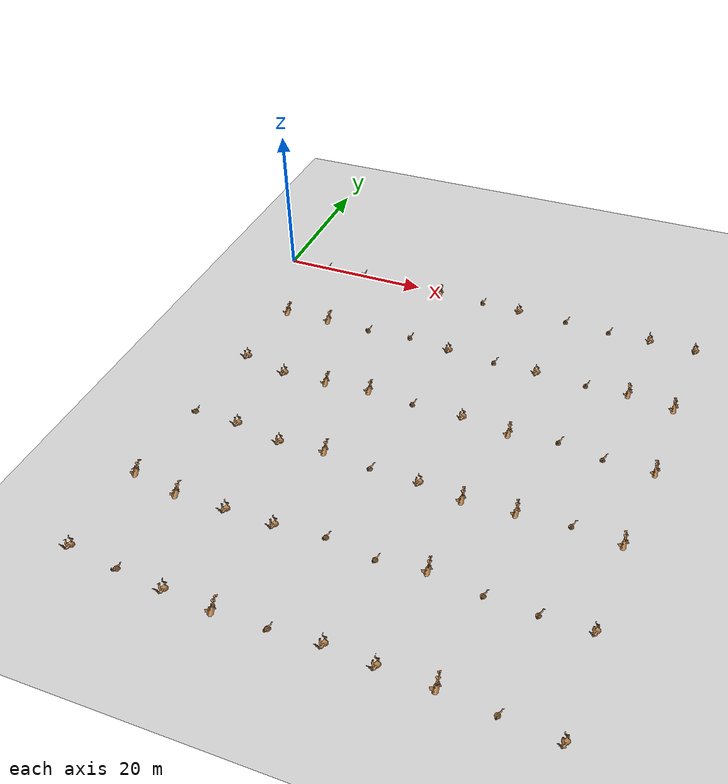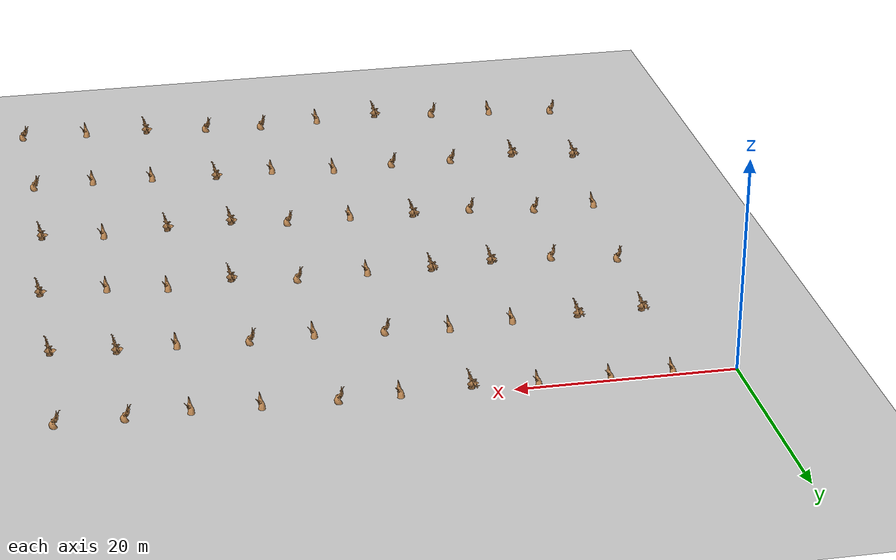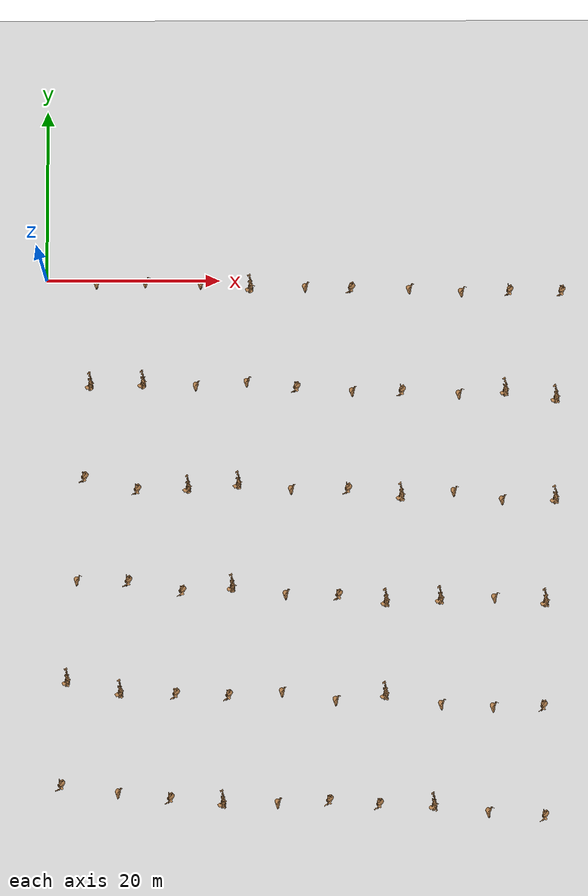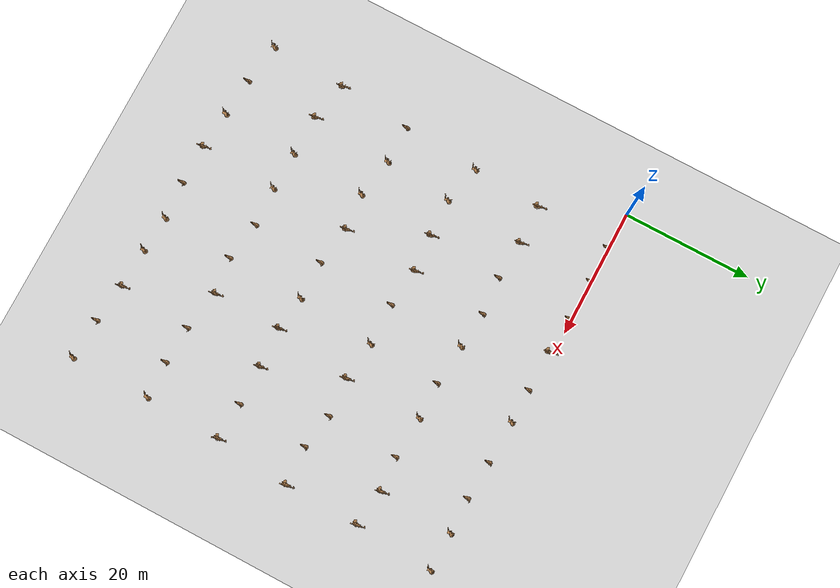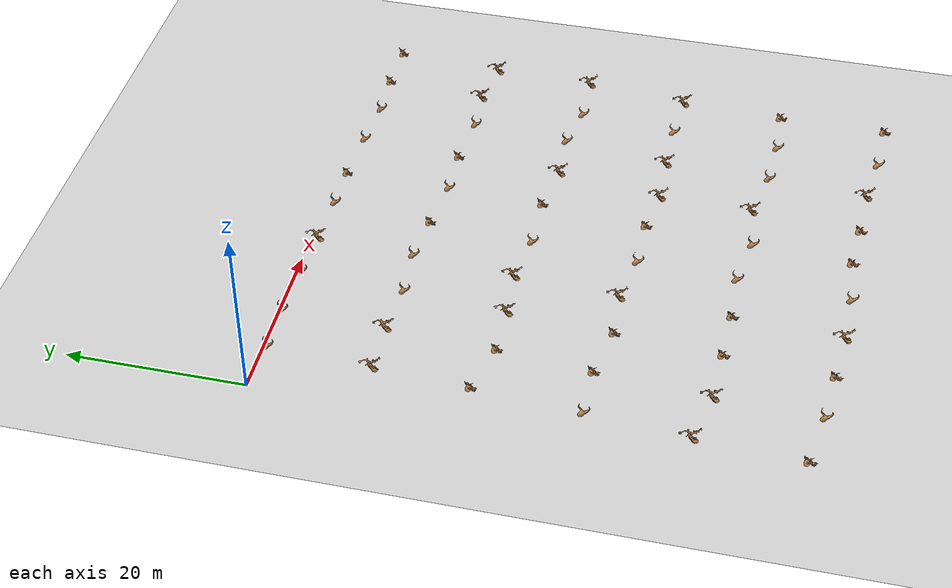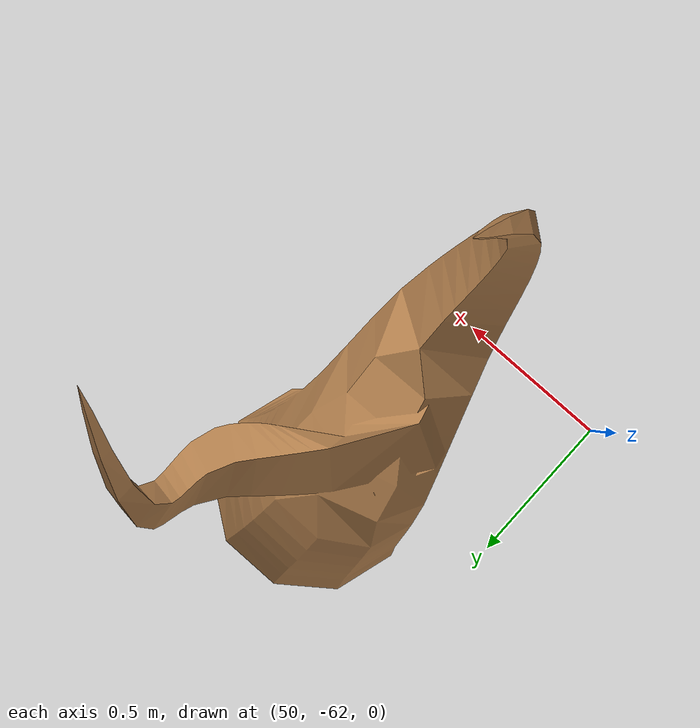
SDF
<sdf version="1.7">
 <world name="default">
  <light name="sun" type="directional">
   <pose>0 0 10 0 -0 0</pose>
   <diffuse>0.8 0.8 0.8 1</diffuse>
   <specular>0.2 0.2 0.2 1</specular>
   <attenuation>
    <range>1000</range>
    <constant>0.9</constant>
    <linear>0.01</linear>
    <quadratic>0.001</quadratic>
   </attenuation>
   <direction>-0.5 0.1 -0.9</direction>
   <spot><inner_angle>0</inner_angle><outer_angle>0</outer_angle><falloff>0</falloff></spot>
  </light>
  <model name="my_ground_plane">
   <static>1</static>
   <link name="link">
    <collision name="collision">
     <pose>27 -27 0 0 -0 0</pose>
     <geometry><plane><normal>0 0 1</normal><size>100 100</size></plane></geometry>
     <surface><friction><ode><mu>100</mu><mu2>50</mu2></ode></friction></surface>
    </collision>
    <visual name="visual">
     <cast_shadows>0</cast_shadows>
     <pose>27 -27 0 0 -0 0</pose>
     <geometry><plane><normal>0 0 1</normal><size>100 100</size></plane></geometry>
     <material>
      <script>
       <uri>model://my_ground_plane/materials/scripts/my_ground_plane.material</uri>
       <uri>model://my_ground_plane/materials/textures/</uri>
       <name>MyGroundPlane/Image</name>
      </script>
     </material>
    </visual>
   </link>
  </model>
  <gravity>0 0 -9.8</gravity>
  <magnetic_field>6e-06 2.3e-05 -4.2e-05</magnetic_field>
  <atmosphere type="adiabatic"/>
  <physics type="ode">
   <max_step_size>0.001</max_step_size>
   <real_time_factor>1</real_time_factor>
   <real_time_update_rate>1000</real_time_update_rate>
  </physics>
  <scene><ambient>0.4 0.4 0.4 1</ambient><background>0.7 0.7 0.7 1</background><shadows>1</shadows></scene>
  <spherical_coordinates>
   <surface_model>EARTH_WGS84</surface_model>
   <latitude_deg>0</latitude_deg>
   <longitude_deg>0</longitude_deg>
   <elevation>0</elevation>
   <heading_deg>0</heading_deg>
  </spherical_coordinates>
  <model name="Vine_growth_00">
   <link name="tree">
    <inertial>
     <mass>10</mass>
     <inertia><ixx>1</ixx><ixy>0</ixy><ixz>0</ixz><iyy>100</iyy><iyz>0</iyz><izz>1</izz></inertia>
    </inertial>
    <collision name="tree_collision">
     <pose>0 0 0 1.57 -0 0</pose>
     <geometry>
      <mesh>
       <scale>0.0065 0.0065 0.0065</scale>
       <uri>/home/jorgeurjc/Jorge_ws/src/patrolling_sim/meshes/Vine/Vine_growth_00.stl</uri>
      </mesh>
     </geometry>
    </collision>
    <visual name="tree_visual">
     <pose>0 0 0 1.57 -0 0</pose>
     <geometry>
      <mesh>
       <scale>0.0065 0.0065 0.0065</scale>
       <uri>/home/jorgeurjc/Jorge_ws/src/patrolling_sim/meshes/Vine/Vine_growth_00.stl</uri>
      </mesh>
     </geometry>
     <material>
      <script><name>Gazebo/Wood</name><uri>file://media/materials/scripts/gazebo.material</uri></script>
     </material>
    </visual>
   </link>
   <pose>5.74212 -0.218962 -1e-05 0.000797 -0 1.57081</pose>
  </model>
  <model name="Vine_growth_00_clone">
   <link name="tree">
    <inertial>
     <mass>10</mass>
     <inertia><ixx>1</ixx><ixy>0</ixy><ixz>0</ixz><iyy>100</iyy><iyz>0</iyz><izz>1</izz></inertia>
    </inertial>
    <collision name="tree_collision">
     <pose>0 0 0 1.57 -0 0</pose>
     <geometry>
      <mesh>
       <scale>0.0065 0.0065 0.0065</scale>
       <uri>/home/jorgeurjc/Jorge_ws/src/patrolling_sim/meshes/Vine/Vine_growth_00.stl</uri>
      </mesh>
     </geometry>
    </collision>
    <visual name="tree_visual">
     <pose>0 0 0 1.57 -0 0</pose>
     <geometry>
      <mesh>
       <scale>0.0065 0.0065 0.0065</scale>
       <uri>/home/jorgeurjc/Jorge_ws/src/patrolling_sim/meshes/Vine/Vine_growth_00.stl</uri>
      </mesh>
     </geometry>
     <material>
      <script><name>Gazebo/Wood</name><uri>file://media/materials/scripts/gazebo.material</uri></script>
     </material>
    </visual>
   </link>
   <pose>11.376 -0.071836 -1e-05 0.000797 -0 1.57081</pose>
  </model>
  <model name="Vine_growth_00_clone_0">
   <link name="tree">
    <inertial>
     <mass>10</mass>
     <inertia><ixx>1</ixx><ixy>0</ixy><ixz>0</ixz><iyy>100</iyy><iyz>0</iyz><izz>1</izz></inertia>
    </inertial>
    <collision name="tree_collision">
     <pose>0 0 0 1.57 -0 0</pose>
     <geometry>
      <mesh>
       <scale>0.0065 0.0065 0.0065</scale>
       <uri>/home/jorgeurjc/Jorge_ws/src/patrolling_sim/meshes/Vine/Vine_growth_00.stl</uri>
      </mesh>
     </geometry>
    </collision>
    <visual name="tree_visual">
     <pose>0 0 0 1.57 -0 0</pose>
     <geometry>
      <mesh>
       <scale>0.0065 0.0065 0.0065</scale>
       <uri>/home/jorgeurjc/Jorge_ws/src/patrolling_sim/meshes/Vine/Vine_growth_00.stl</uri>
      </mesh>
     </geometry>
     <material>
      <script><name>Gazebo/Wood</name><uri>file://media/materials/scripts/gazebo.material</uri></script>
     </material>
    </visual>
   </link>
   <pose>17.7576 -0.286098 -1e-05 0.000797 -0 1.57081</pose>
  </model>
  <model name="Vine_growth_00_clone_1">
   <link name="tree">
    <inertial>
     <mass>10</mass>
     <inertia><ixx>1</ixx><ixy>0</ixy><ixz>0</ixz><iyy>100</iyy><iyz>0</iyz><izz>1</izz></inertia>
    </inertial>
    <collision name="tree_collision">
     <pose>0 0 0 1.57 -0 0</pose>
     <geometry>
      <mesh>
       <scale>0.0065 0.0065 0.0065</scale>
       <uri>/home/jorgeurjc/Jorge_ws/src/patrolling_sim/meshes/Vine/Vine_growth_00.stl</uri>
      </mesh>
     </geometry>
    </collision>
    <visual name="tree_visual">
     <pose>0 0 0 1.57 -0 0</pose>
     <geometry>
      <mesh>
       <scale>0.0065 0.0065 0.0065</scale>
       <uri>/home/jorgeurjc/Jorge_ws/src/patrolling_sim/meshes/Vine/Vine_growth_00.stl</uri>
      </mesh>
     </geometry>
     <material>
      <script><name>Gazebo/Wood</name><uri>file://media/materials/scripts/gazebo.material</uri></script>
     </material>
    </visual>
   </link>
   <pose>29.8378 -0.631978 -1e-05 0.000797 -0 1.57081</pose>
  </model>
  <model name="Vine_growth_00_clone_2">
   <link name="tree">
    <inertial>
     <mass>10</mass>
     <inertia><ixx>1</ixx><ixy>0</ixy><ixz>0</ixz><iyy>100</iyy><iyz>0</iyz><izz>1</izz></inertia>
    </inertial>
    <collision name="tree_collision">
     <pose>0 0 0 1.57 -0 0</pose>
     <geometry>
      <mesh>
       <scale>0.0065 0.0065 0.0065</scale>
       <uri>/home/jorgeurjc/Jorge_ws/src/patrolling_sim/meshes/Vine/Vine_growth_00.stl</uri>
      </mesh>
     </geometry>
    </collision>
    <visual name="tree_visual">
     <pose>0 0 0 1.57 -0 0</pose>
     <geometry>
      <mesh>
       <scale>0.0065 0.0065 0.0065</scale>
       <uri>/home/jorgeurjc/Jorge_ws/src/patrolling_sim/meshes/Vine/Vine_growth_00.stl</uri>
      </mesh>
     </geometry>
     <material>
      <script><name>Gazebo/Wood</name><uri>file://media/materials/scripts/gazebo.material</uri></script>
     </material>
    </visual>
   </link>
   <pose>41.8695 -0.859949 -1e-05 0.000797 -0 1.57081</pose>
  </model>
  <model name="Vine_growth_00_clone_3">
   <link name="tree">
    <inertial>
     <mass>10</mass>
     <inertia><ixx>1</ixx><ixy>0</ixy><ixz>0</ixz><iyy>100</iyy><iyz>0</iyz><izz>1</izz></inertia>
    </inertial>
    <collision name="tree_collision">
     <pose>0 0 0 1.57 -0 0</pose>
     <geometry>
      <mesh>
       <scale>0.0065 0.0065 0.0065</scale>
       <uri>/home/jorgeurjc/Jorge_ws/src/patrolling_sim/meshes/Vine/Vine_growth_00.stl</uri>
      </mesh>
     </geometry>
    </collision>
    <visual name="tree_visual">
     <pose>0 0 0 1.57 -0 0</pose>
     <geometry>
      <mesh>
       <scale>0.0065 0.0065 0.0065</scale>
       <uri>/home/jorgeurjc/Jorge_ws/src/patrolling_sim/meshes/Vine/Vine_growth_00.stl</uri>
      </mesh>
     </geometry>
     <material>
      <script><name>Gazebo/Wood</name><uri>file://media/materials/scripts/gazebo.material</uri></script>
     </material>
    </visual>
   </link>
   <pose>47.8975 -1.20692 -1e-05 0.000797 -0 1.57081</pose>
  </model>
  <model name="Vine_growth_00_clone_4">
   <link name="tree">
    <inertial>
     <mass>10</mass>
     <inertia><ixx>1</ixx><ixy>0</ixy><ixz>0</ixz><iyy>100</iyy><iyz>0</iyz><izz>1</izz></inertia>
    </inertial>
    <collision name="tree_collision">
     <pose>0 0 0 1.57 -0 0</pose>
     <geometry>
      <mesh>
       <scale>0.0065 0.0065 0.0065</scale>
       <uri>/home/jorgeurjc/Jorge_ws/src/patrolling_sim/meshes/Vine/Vine_growth_00.stl</uri>
      </mesh>
     </geometry>
    </collision>
    <visual name="tree_visual">
     <pose>0 0 0 1.57 -0 0</pose>
     <geometry>
      <mesh>
       <scale>0.0065 0.0065 0.0065</scale>
       <uri>/home/jorgeurjc/Jorge_ws/src/patrolling_sim/meshes/Vine/Vine_growth_00.stl</uri>
      </mesh>
     </geometry>
     <material>
      <script><name>Gazebo/Wood</name><uri>file://media/materials/scripts/gazebo.material</uri></script>
     </material>
    </visual>
   </link>
   <pose>47.5243 -13.1738 -1e-05 0.000797 -0 1.57081</pose>
  </model>
  <model name="Vine_growth_00_clone_5">
   <link name="tree">
    <inertial>
     <mass>10</mass>
     <inertia><ixx>1</ixx><ixy>0</ixy><ixz>0</ixz><iyy>100</iyy><iyz>0</iyz><izz>1</izz></inertia>
    </inertial>
    <collision name="tree_collision">
     <pose>0 0 0 1.57 -0 0</pose>
     <geometry>
      <mesh>
       <scale>0.0065 0.0065 0.0065</scale>
       <uri>/home/jorgeurjc/Jorge_ws/src/patrolling_sim/meshes/Vine/Vine_growth_00.stl</uri>
      </mesh>
     </geometry>
    </collision>
    <visual name="tree_visual">
     <pose>0 0 0 1.57 -0 0</pose>
     <geometry>
      <mesh>
       <scale>0.0065 0.0065 0.0065</scale>
       <uri>/home/jorgeurjc/Jorge_ws/src/patrolling_sim/meshes/Vine/Vine_growth_00.stl</uri>
      </mesh>
     </geometry>
     <material>
      <script><name>Gazebo/Wood</name><uri>file://media/materials/scripts/gazebo.material</uri></script>
     </material>
    </visual>
   </link>
   <pose>35.2384 -12.8705 -1e-05 0.000797 -0 1.57081</pose>
  </model>
  <model name="Vine_growth_00_clone_6">
   <link name="tree">
    <inertial>
     <mass>10</mass>
     <inertia><ixx>1</ixx><ixy>0</ixy><ixz>0</ixz><iyy>100</iyy><iyz>0</iyz><izz>1</izz></inertia>
    </inertial>
    <collision name="tree_collision">
     <pose>0 0 0 1.57 -0 0</pose>
     <geometry>
      <mesh>
       <scale>0.0065 0.0065 0.0065</scale>
       <uri>/home/jorgeurjc/Jorge_ws/src/patrolling_sim/meshes/Vine/Vine_growth_00.stl</uri>
      </mesh>
     </geometry>
    </collision>
    <visual name="tree_visual">
     <pose>0 0 0 1.57 -0 0</pose>
     <geometry>
      <mesh>
       <scale>0.0065 0.0065 0.0065</scale>
       <uri>/home/jorgeurjc/Jorge_ws/src/patrolling_sim/meshes/Vine/Vine_growth_00.stl</uri>
      </mesh>
     </geometry>
     <material>
      <script><name>Gazebo/Wood</name><uri>file://media/materials/scripts/gazebo.material</uri></script>
     </material>
    </visual>
   </link>
   <pose>17.2249 -12.2046 -1e-05 0.000797 -0 1.57081</pose>
  </model>
  <model name="Vine_growth_00_clone_7">
   <link name="tree">
    <inertial>
     <mass>10</mass>
     <inertia><ixx>1</ixx><ixy>0</ixy><ixz>0</ixz><iyy>100</iyy><iyz>0</iyz><izz>1</izz></inertia>
    </inertial>
    <collision name="tree_collision">
     <pose>0 0 0 1.57 -0 0</pose>
     <geometry>
      <mesh>
       <scale>0.0065 0.0065 0.0065</scale>
       <uri>/home/jorgeurjc/Jorge_ws/src/patrolling_sim/meshes/Vine/Vine_growth_00.stl</uri>
      </mesh>
     </geometry>
    </collision>
    <visual name="tree_visual">
     <pose>0 0 0 1.57 -0 0</pose>
     <geometry>
      <mesh>
       <scale>0.0065 0.0065 0.0065</scale>
       <uri>/home/jorgeurjc/Jorge_ws/src/patrolling_sim/meshes/Vine/Vine_growth_00.stl</uri>
      </mesh>
     </geometry>
     <material>
      <script><name>Gazebo/Wood</name><uri>file://media/materials/scripts/gazebo.material</uri></script>
     </material>
    </visual>
   </link>
   <pose>23.0908 -11.7377 -1e-05 0.000797 -0 1.57081</pose>
  </model>
  <model name="Vine_growth_00_clone_8">
   <link name="tree">
    <inertial>
     <mass>10</mass>
     <inertia><ixx>1</ixx><ixy>0</ixy><ixz>0</ixz><iyy>100</iyy><iyz>0</iyz><izz>1</izz></inertia>
    </inertial>
    <collision name="tree_collision">
     <pose>0 0 0 1.57 -0 0</pose>
     <geometry>
      <mesh>
       <scale>0.0065 0.0065 0.0065</scale>
       <uri>/home/jorgeurjc/Jorge_ws/src/patrolling_sim/meshes/Vine/Vine_growth_00.stl</uri>
      </mesh>
     </geometry>
    </collision>
    <visual name="tree_visual">
     <pose>0 0 0 1.57 -0 0</pose>
     <geometry>
      <mesh>
       <scale>0.0065 0.0065 0.0065</scale>
       <uri>/home/jorgeurjc/Jorge_ws/src/patrolling_sim/meshes/Vine/Vine_growth_00.stl</uri>
      </mesh>
     </geometry>
     <material>
      <script><name>Gazebo/Wood</name><uri>file://media/materials/scripts/gazebo.material</uri></script>
     </material>
    </visual>
   </link>
   <pose>28.1973 -24.2593 -1e-05 0.000797 -0 1.57081</pose>
  </model>
  <model name="Vine_growth_00_clone_9">
   <link name="tree">
    <inertial>
     <mass>10</mass>
     <inertia><ixx>1</ixx><ixy>0</ixy><ixz>0</ixz><iyy>100</iyy><iyz>0</iyz><izz>1</izz></inertia>
    </inertial>
    <collision name="tree_collision">
     <pose>0 0 0 1.57 -0 0</pose>
     <geometry>
      <mesh>
       <scale>0.0065 0.0065 0.0065</scale>
       <uri>/home/jorgeurjc/Jorge_ws/src/patrolling_sim/meshes/Vine/Vine_growth_00.stl</uri>
      </mesh>
     </geometry>
    </collision>
    <visual name="tree_visual">
     <pose>0 0 0 1.57 -0 0</pose>
     <geometry>
      <mesh>
       <scale>0.0065 0.0065 0.0065</scale>
       <uri>/home/jorgeurjc/Jorge_ws/src/patrolling_sim/meshes/Vine/Vine_growth_00.stl</uri>
      </mesh>
     </geometry>
     <material>
      <script><name>Gazebo/Wood</name><uri>file://media/materials/scripts/gazebo.material</uri></script>
     </material>
    </visual>
   </link>
   <pose>27.5565 -36.3879 -1e-05 0.000797 -0 1.57081</pose>
  </model>
  <model name="Vine_growth_00_clone_10">
   <link name="tree">
    <inertial>
     <mass>10</mass>
     <inertia><ixx>1</ixx><ixy>0</ixy><ixz>0</ixz><iyy>100</iyy><iyz>0</iyz><izz>1</izz></inertia>
    </inertial>
    <collision name="tree_collision">
     <pose>0 0 0 1.57 -0 0</pose>
     <geometry>
      <mesh>
       <scale>0.0065 0.0065 0.0065</scale>
       <uri>/home/jorgeurjc/Jorge_ws/src/patrolling_sim/meshes/Vine/Vine_growth_00.stl</uri>
      </mesh>
     </geometry>
    </collision>
    <visual name="tree_visual">
     <pose>0 0 0 1.57 -0 0</pose>
     <geometry>
      <mesh>
       <scale>0.0065 0.0065 0.0065</scale>
       <uri>/home/jorgeurjc/Jorge_ws/src/patrolling_sim/meshes/Vine/Vine_growth_00.stl</uri>
      </mesh>
     </geometry>
     <material>
      <script><name>Gazebo/Wood</name><uri>file://media/materials/scripts/gazebo.material</uri></script>
     </material>
    </visual>
   </link>
   <pose>51.4261 -36.8203 -1e-05 0.000797 -0 1.57081</pose>
  </model>
  <model name="Vine_growth_00_clone_11">
   <link name="tree">
    <inertial>
     <mass>10</mass>
     <inertia><ixx>1</ixx><ixy>0</ixy><ixz>0</ixz><iyy>100</iyy><iyz>0</iyz><izz>1</izz></inertia>
    </inertial>
    <collision name="tree_collision">
     <pose>0 0 0 1.57 -0 0</pose>
     <geometry>
      <mesh>
       <scale>0.0065 0.0065 0.0065</scale>
       <uri>/home/jorgeurjc/Jorge_ws/src/patrolling_sim/meshes/Vine/Vine_growth_00.stl</uri>
      </mesh>
     </geometry>
    </collision>
    <visual name="tree_visual">
     <pose>0 0 0 1.57 -0 0</pose>
     <geometry>
      <mesh>
       <scale>0.0065 0.0065 0.0065</scale>
       <uri>/home/jorgeurjc/Jorge_ws/src/patrolling_sim/meshes/Vine/Vine_growth_00.stl</uri>
      </mesh>
     </geometry>
     <material>
      <script><name>Gazebo/Wood</name><uri>file://media/materials/scripts/gazebo.material</uri></script>
     </material>
    </visual>
   </link>
   <pose>46.8505 -24.5299 -1e-05 0.000797 -0 1.57081</pose>
  </model>
  <model name="Vine_growth_00_clone_12">
   <link name="tree">
    <inertial>
     <mass>10</mass>
     <inertia><ixx>1</ixx><ixy>0</ixy><ixz>0</ixz><iyy>100</iyy><iyz>0</iyz><izz>1</izz></inertia>
    </inertial>
    <collision name="tree_collision">
     <pose>0 0 0 1.57 -0 0</pose>
     <geometry>
      <mesh>
       <scale>0.0065 0.0065 0.0065</scale>
       <uri>/home/jorgeurjc/Jorge_ws/src/patrolling_sim/meshes/Vine/Vine_growth_00.stl</uri>
      </mesh>
     </geometry>
    </collision>
    <visual name="tree_visual">
     <pose>0 0 0 1.57 -0 0</pose>
     <geometry>
      <mesh>
       <scale>0.0065 0.0065 0.0065</scale>
       <uri>/home/jorgeurjc/Jorge_ws/src/patrolling_sim/meshes/Vine/Vine_growth_00.stl</uri>
      </mesh>
     </geometry>
     <material>
      <script><name>Gazebo/Wood</name><uri>file://media/materials/scripts/gazebo.material</uri></script>
     </material>
    </visual>
   </link>
   <pose>52.3952 -25.5047 -1e-05 0.000797 -0 1.57081</pose>
  </model>
  <model name="Vine_growth_00_clone_13">
   <link name="tree">
    <inertial>
     <mass>10</mass>
     <inertia><ixx>1</ixx><ixy>0</ixy><ixz>0</ixz><iyy>100</iyy><iyz>0</iyz><izz>1</izz></inertia>
    </inertial>
    <collision name="tree_collision">
     <pose>0 0 0 1.57 -0 0</pose>
     <geometry>
      <mesh>
       <scale>0.0065 0.0065 0.0065</scale>
       <uri>/home/jorgeurjc/Jorge_ws/src/patrolling_sim/meshes/Vine/Vine_growth_00.stl</uri>
      </mesh>
     </geometry>
    </collision>
    <visual name="tree_visual">
     <pose>0 0 0 1.57 -0 0</pose>
     <geometry>
      <mesh>
       <scale>0.0065 0.0065 0.0065</scale>
       <uri>/home/jorgeurjc/Jorge_ws/src/patrolling_sim/meshes/Vine/Vine_growth_00.stl</uri>
      </mesh>
     </geometry>
     <material>
      <script><name>Gazebo/Wood</name><uri>file://media/materials/scripts/gazebo.material</uri></script>
     </material>
    </visual>
   </link>
   <pose>27.1323 -47.5768 -1e-05 0.000797 -0 1.57081</pose>
  </model>
  <model name="Vine_growth_00_clone_14">
   <link name="tree">
    <inertial>
     <mass>10</mass>
     <inertia><ixx>1</ixx><ixy>0</ixy><ixz>0</ixz><iyy>100</iyy><iyz>0</iyz><izz>1</izz></inertia>
    </inertial>
    <collision name="tree_collision">
     <pose>0 0 0 1.57 -0 0</pose>
     <geometry>
      <mesh>
       <scale>0.0065 0.0065 0.0065</scale>
       <uri>/home/jorgeurjc/Jorge_ws/src/patrolling_sim/meshes/Vine/Vine_growth_00.stl</uri>
      </mesh>
     </geometry>
    </collision>
    <visual name="tree_visual">
     <pose>0 0 0 1.57 -0 0</pose>
     <geometry>
      <mesh>
       <scale>0.0065 0.0065 0.0065</scale>
       <uri>/home/jorgeurjc/Jorge_ws/src/patrolling_sim/meshes/Vine/Vine_growth_00.stl</uri>
      </mesh>
     </geometry>
     <material>
      <script><name>Gazebo/Wood</name><uri>file://media/materials/scripts/gazebo.material</uri></script>
     </material>
    </visual>
   </link>
   <pose>33.2486 -48.5558 -1e-05 0.000797 -0 1.57081</pose>
  </model>
  <model name="Vine_growth_00_clone_15">
   <link name="tree">
    <inertial>
     <mass>10</mass>
     <inertia><ixx>1</ixx><ixy>0</ixy><ixz>0</ixz><iyy>100</iyy><iyz>0</iyz><izz>1</izz></inertia>
    </inertial>
    <collision name="tree_collision">
     <pose>0 0 0 1.57 -0 0</pose>
     <geometry>
      <mesh>
       <scale>0.0065 0.0065 0.0065</scale>
       <uri>/home/jorgeurjc/Jorge_ws/src/patrolling_sim/meshes/Vine/Vine_growth_00.stl</uri>
      </mesh>
     </geometry>
    </collision>
    <visual name="tree_visual">
     <pose>0 0 0 1.57 -0 0</pose>
     <geometry>
      <mesh>
       <scale>0.0065 0.0065 0.0065</scale>
       <uri>/home/jorgeurjc/Jorge_ws/src/patrolling_sim/meshes/Vine/Vine_growth_00.stl</uri>
      </mesh>
     </geometry>
     <material>
      <script><name>Gazebo/Wood</name><uri>file://media/materials/scripts/gazebo.material</uri></script>
     </material>
    </visual>
   </link>
   <pose>51.1457 -49.3432 -1e-05 0.000797 -0 1.57081</pose>
  </model>
  <model name="Vine_growth_00_clone_16">
   <link name="tree">
    <inertial>
     <mass>10</mass>
     <inertia><ixx>1</ixx><ixy>0</ixy><ixz>0</ixz><iyy>100</iyy><iyz>0</iyz><izz>1</izz></inertia>
    </inertial>
    <collision name="tree_collision">
     <pose>0 0 0 1.57 -0 0</pose>
     <geometry>
      <mesh>
       <scale>0.0065 0.0065 0.0065</scale>
       <uri>/home/jorgeurjc/Jorge_ws/src/patrolling_sim/meshes/Vine/Vine_growth_00.stl</uri>
      </mesh>
     </geometry>
    </collision>
    <visual name="tree_visual">
     <pose>0 0 0 1.57 -0 0</pose>
     <geometry>
      <mesh>
       <scale>0.0065 0.0065 0.0065</scale>
       <uri>/home/jorgeurjc/Jorge_ws/src/patrolling_sim/meshes/Vine/Vine_growth_00.stl</uri>
      </mesh>
     </geometry>
     <material>
      <script><name>Gazebo/Wood</name><uri>file://media/materials/scripts/gazebo.material</uri></script>
     </material>
    </visual>
   </link>
   <pose>45.2617 -49.0311 -1e-05 0.000797 -0 1.57081</pose>
  </model>
  <model name="Vine_growth_00_clone_17">
   <link name="tree">
    <inertial>
     <mass>10</mass>
     <inertia><ixx>1</ixx><ixy>0</ixy><ixz>0</ixz><iyy>100</iyy><iyz>0</iyz><izz>1</izz></inertia>
    </inertial>
    <collision name="tree_collision">
     <pose>0 0 0 1.57 -0 0</pose>
     <geometry>
      <mesh>
       <scale>0.0065 0.0065 0.0065</scale>
       <uri>/home/jorgeurjc/Jorge_ws/src/patrolling_sim/meshes/Vine/Vine_growth_00.stl</uri>
      </mesh>
     </geometry>
    </collision>
    <visual name="tree_visual">
     <pose>0 0 0 1.57 -0 0</pose>
     <geometry>
      <mesh>
       <scale>0.0065 0.0065 0.0065</scale>
       <uri>/home/jorgeurjc/Jorge_ws/src/patrolling_sim/meshes/Vine/Vine_growth_00.stl</uri>
      </mesh>
     </geometry>
     <material>
      <script><name>Gazebo/Wood</name><uri>file://media/materials/scripts/gazebo.material</uri></script>
     </material>
    </visual>
   </link>
   <pose>50.5403 -61.2807 -1e-05 0.000797 -0 1.57081</pose>
  </model>
  <model name="Vine_growth_00_clone_18">
   <link name="tree">
    <inertial>
     <mass>10</mass>
     <inertia><ixx>1</ixx><ixy>0</ixy><ixz>0</ixz><iyy>100</iyy><iyz>0</iyz><izz>1</izz></inertia>
    </inertial>
    <collision name="tree_collision">
     <pose>0 0 0 1.57 -0 0</pose>
     <geometry>
      <mesh>
       <scale>0.0065 0.0065 0.0065</scale>
       <uri>/home/jorgeurjc/Jorge_ws/src/patrolling_sim/meshes/Vine/Vine_growth_00.stl</uri>
      </mesh>
     </geometry>
    </collision>
    <visual name="tree_visual">
     <pose>0 0 0 1.57 -0 0</pose>
     <geometry>
      <mesh>
       <scale>0.0065 0.0065 0.0065</scale>
       <uri>/home/jorgeurjc/Jorge_ws/src/patrolling_sim/meshes/Vine/Vine_growth_00.stl</uri>
      </mesh>
     </geometry>
     <material>
      <script><name>Gazebo/Wood</name><uri>file://media/materials/scripts/gazebo.material</uri></script>
     </material>
    </visual>
   </link>
   <pose>26.6302 -60.2184 -1e-05 0.000797 -0 1.57081</pose>
  </model>
  <model name="Vine_growth_00_clone_19">
   <link name="tree">
    <inertial>
     <mass>10</mass>
     <inertia><ixx>1</ixx><ixy>0</ixy><ixz>0</ixz><iyy>100</iyy><iyz>0</iyz><izz>1</izz></inertia>
    </inertial>
    <collision name="tree_collision">
     <pose>0 0 0 1.57 -0 0</pose>
     <geometry>
      <mesh>
       <scale>0.0065 0.0065 0.0065</scale>
       <uri>/home/jorgeurjc/Jorge_ws/src/patrolling_sim/meshes/Vine/Vine_growth_00.stl</uri>
      </mesh>
     </geometry>
    </collision>
    <visual name="tree_visual">
     <pose>0 0 0 1.57 -0 0</pose>
     <geometry>
      <mesh>
       <scale>0.0065 0.0065 0.0065</scale>
       <uri>/home/jorgeurjc/Jorge_ws/src/patrolling_sim/meshes/Vine/Vine_growth_00.stl</uri>
      </mesh>
     </geometry>
     <material>
      <script><name>Gazebo/Wood</name><uri>file://media/materials/scripts/gazebo.material</uri></script>
     </material>
    </visual>
   </link>
   <pose>8.51385 -59.0696 -1e-05 0.000797 -0 1.57081</pose>
  </model>
  <model name="Vine_growth_00_clone_20">
   <link name="tree">
    <inertial>
     <mass>10</mass>
     <inertia><ixx>1</ixx><ixy>0</ixy><ixz>0</ixz><iyy>100</iyy><iyz>0</iyz><izz>1</izz></inertia>
    </inertial>
    <collision name="tree_collision">
     <pose>0 0 0 1.57 -0 0</pose>
     <geometry>
      <mesh>
       <scale>0.0065 0.0065 0.0065</scale>
       <uri>/home/jorgeurjc/Jorge_ws/src/patrolling_sim/meshes/Vine/Vine_growth_00.stl</uri>
      </mesh>
     </geometry>
    </collision>
    <visual name="tree_visual">
     <pose>0 0 0 1.57 -0 0</pose>
     <geometry>
      <mesh>
       <scale>0.0065 0.0065 0.0065</scale>
       <uri>/home/jorgeurjc/Jorge_ws/src/patrolling_sim/meshes/Vine/Vine_growth_00.stl</uri>
      </mesh>
     </geometry>
     <material>
      <script><name>Gazebo/Wood</name><uri>file://media/materials/scripts/gazebo.material</uri></script>
     </material>
    </visual>
   </link>
   <pose>3.67248 -34.7603 -1e-05 0.000797 -0 1.57081</pose>
  </model>
  <model name="Vine_growth_02_clone">
   <link name="tree">
    <inertial>
     <mass>10</mass>
     <inertia><ixx>1</ixx><ixy>0</ixy><ixz>0</ixz><iyy>100</iyy><iyz>0</iyz><izz>1</izz></inertia>
    </inertial>
    <collision name="tree_collision">
     <pose>0 0 0 1.57 -0 0</pose>
     <geometry>
      <mesh>
       <scale>0.0065 0.0065 0.0065</scale>
       <uri>/home/jorgeurjc/Jorge_ws/src/patrolling_sim/meshes/Vine/Vine_growth_02.stl</uri>
      </mesh>
     </geometry>
    </collision>
    <visual name="tree_visual">
     <pose>0 0 0 1.57 -0 0</pose>
     <geometry>
      <mesh>
       <scale>0.0065 0.0065 0.0065</scale>
       <uri>/home/jorgeurjc/Jorge_ws/src/patrolling_sim/meshes/Vine/Vine_growth_02.stl</uri>
      </mesh>
     </geometry>
     <material>
      <script><name>Gazebo/Wood</name><uri>file://media/materials/scripts/gazebo.material</uri></script>
     </material>
    </visual>
   </link>
   <pose>16.3828 -24.5608 0 0.000796 -0 1.58396</pose>
  </model>
  <model name="Vine_growth_02_clone_0">
   <link name="tree">
    <inertial>
     <mass>10</mass>
     <inertia><ixx>1</ixx><ixy>0</ixy><ixz>0</ixz><iyy>100</iyy><iyz>0</iyz><izz>1</izz></inertia>
    </inertial>
    <collision name="tree_collision">
     <pose>0 0 0 1.57 -0 0</pose>
     <geometry>
      <mesh>
       <scale>0.0065 0.0065 0.0065</scale>
       <uri>/home/jorgeurjc/Jorge_ws/src/patrolling_sim/meshes/Vine/Vine_growth_02.stl</uri>
      </mesh>
     </geometry>
    </collision>
    <visual name="tree_visual">
     <pose>0 0 0 1.57 -0 0</pose>
     <geometry>
      <mesh>
       <scale>0.0065 0.0065 0.0065</scale>
       <uri>/home/jorgeurjc/Jorge_ws/src/patrolling_sim/meshes/Vine/Vine_growth_02.stl</uri>
      </mesh>
     </geometry>
     <material>
      <script><name>Gazebo/Wood</name><uri>file://media/materials/scripts/gazebo.material</uri></script>
     </material>
    </visual>
   </link>
   <pose>11.1591 -12.3686 0 0.000796 -0 1.58396</pose>
  </model>
  <model name="Vine_growth_02_clone_1">
   <link name="tree">
    <inertial>
     <mass>10</mass>
     <inertia><ixx>1</ixx><ixy>0</ixy><ixz>0</ixz><iyy>100</iyy><iyz>0</iyz><izz>1</izz></inertia>
    </inertial>
    <collision name="tree_collision">
     <pose>0 0 0 1.57 -0 0</pose>
     <geometry>
      <mesh>
       <scale>0.0065 0.0065 0.0065</scale>
       <uri>/home/jorgeurjc/Jorge_ws/src/patrolling_sim/meshes/Vine/Vine_growth_02.stl</uri>
      </mesh>
     </geometry>
    </collision>
    <visual name="tree_visual">
     <pose>0 0 0 1.57 -0 0</pose>
     <geometry>
      <mesh>
       <scale>0.0065 0.0065 0.0065</scale>
       <uri>/home/jorgeurjc/Jorge_ws/src/patrolling_sim/meshes/Vine/Vine_growth_02.stl</uri>
      </mesh>
     </geometry>
     <material>
      <script><name>Gazebo/Wood</name><uri>file://media/materials/scripts/gazebo.material</uri></script>
     </material>
    </visual>
   </link>
   <pose>5.10718 -12.5521 1e-06 0.000797 2e-06 1.58397</pose>
  </model>
  <model name="Vine_growth_02_clone_2">
   <link name="tree">
    <inertial>
     <mass>10</mass>
     <inertia><ixx>1</ixx><ixy>0</ixy><ixz>0</ixz><iyy>100</iyy><iyz>0</iyz><izz>1</izz></inertia>
    </inertial>
    <collision name="tree_collision">
     <pose>0 0 0 1.57 -0 0</pose>
     <geometry>
      <mesh>
       <scale>0.0065 0.0065 0.0065</scale>
       <uri>/home/jorgeurjc/Jorge_ws/src/patrolling_sim/meshes/Vine/Vine_growth_02.stl</uri>
      </mesh>
     </geometry>
    </collision>
    <visual name="tree_visual">
     <pose>0 0 0 1.57 -0 0</pose>
     <geometry>
      <mesh>
       <scale>0.0065 0.0065 0.0065</scale>
       <uri>/home/jorgeurjc/Jorge_ws/src/patrolling_sim/meshes/Vine/Vine_growth_02.stl</uri>
      </mesh>
     </geometry>
     <material>
      <script><name>Gazebo/Wood</name><uri>file://media/materials/scripts/gazebo.material</uri></script>
     </material>
    </visual>
   </link>
   <pose>23.5208 -1.11353 1e-06 0.000797 2e-06 1.58395</pose>
  </model>
  <model name="Vine_growth_02_clone_3">
   <link name="tree">
    <inertial>
     <mass>10</mass>
     <inertia><ixx>1</ixx><ixy>0</ixy><ixz>0</ixz><iyy>100</iyy><iyz>0</iyz><izz>1</izz></inertia>
    </inertial>
    <collision name="tree_collision">
     <pose>0 0 0 1.57 -0 0</pose>
     <geometry>
      <mesh>
       <scale>0.0065 0.0065 0.0065</scale>
       <uri>/home/jorgeurjc/Jorge_ws/src/patrolling_sim/meshes/Vine/Vine_growth_02.stl</uri>
      </mesh>
     </geometry>
    </collision>
    <visual name="tree_visual">
     <pose>0 0 0 1.57 -0 0</pose>
     <geometry>
      <mesh>
       <scale>0.0065 0.0065 0.0065</scale>
       <uri>/home/jorgeurjc/Jorge_ws/src/patrolling_sim/meshes/Vine/Vine_growth_02.stl</uri>
      </mesh>
     </geometry>
     <material>
      <script><name>Gazebo/Wood</name><uri>file://media/materials/scripts/gazebo.material</uri></script>
     </material>
    </visual>
   </link>
   <pose>58.7192 -14.1265 0 0.000796 -0 1.58395</pose>
  </model>
  <model name="Vine_growth_02_clone_4">
   <link name="tree">
    <inertial>
     <mass>10</mass>
     <inertia><ixx>1</ixx><ixy>0</ixy><ixz>0</ixz><iyy>100</iyy><iyz>0</iyz><izz>1</izz></inertia>
    </inertial>
    <collision name="tree_collision">
     <pose>0 0 0 1.57 -0 0</pose>
     <geometry>
      <mesh>
       <scale>0.0065 0.0065 0.0065</scale>
       <uri>/home/jorgeurjc/Jorge_ws/src/patrolling_sim/meshes/Vine/Vine_growth_02.stl</uri>
      </mesh>
     </geometry>
    </collision>
    <visual name="tree_visual">
     <pose>0 0 0 1.57 -0 0</pose>
     <geometry>
      <mesh>
       <scale>0.0065 0.0065 0.0065</scale>
       <uri>/home/jorgeurjc/Jorge_ws/src/patrolling_sim/meshes/Vine/Vine_growth_02.stl</uri>
      </mesh>
     </geometry>
     <material>
      <script><name>Gazebo/Wood</name><uri>file://media/materials/scripts/gazebo.material</uri></script>
     </material>
    </visual>
   </link>
   <pose>40.8462 -25.4946 0 0.000796 -0 1.58396</pose>
  </model>
  <model name="Vine_growth_02_clone_5">
   <link name="tree">
    <inertial>
     <mass>10</mass>
     <inertia><ixx>1</ixx><ixy>0</ixy><ixz>0</ixz><iyy>100</iyy><iyz>0</iyz><izz>1</izz></inertia>
    </inertial>
    <collision name="tree_collision">
     <pose>0 0 0 1.57 -0 0</pose>
     <geometry>
      <mesh>
       <scale>0.0065 0.0065 0.0065</scale>
       <uri>/home/jorgeurjc/Jorge_ws/src/patrolling_sim/meshes/Vine/Vine_growth_02.stl</uri>
      </mesh>
     </geometry>
    </collision>
    <visual name="tree_visual">
     <pose>0 0 0 1.57 -0 0</pose>
     <geometry>
      <mesh>
       <scale>0.0065 0.0065 0.0065</scale>
       <uri>/home/jorgeurjc/Jorge_ws/src/patrolling_sim/meshes/Vine/Vine_growth_02.stl</uri>
      </mesh>
     </geometry>
     <material>
      <script><name>Gazebo/Wood</name><uri>file://media/materials/scripts/gazebo.material</uri></script>
     </material>
    </visual>
   </link>
   <pose>39.0438 -37.7032 0 0.000796 -0 1.58395</pose>
  </model>
  <model name="Vine_growth_02_clone_6">
   <link name="tree">
    <inertial>
     <mass>10</mass>
     <inertia><ixx>1</ixx><ixy>0</ixy><ixz>0</ixz><iyy>100</iyy><iyz>0</iyz><izz>1</izz></inertia>
    </inertial>
    <collision name="tree_collision">
     <pose>0 0 0 1.57 -0 0</pose>
     <geometry>
      <mesh>
       <scale>0.0065 0.0065 0.0065</scale>
       <uri>/home/jorgeurjc/Jorge_ws/src/patrolling_sim/meshes/Vine/Vine_growth_02.stl</uri>
      </mesh>
     </geometry>
    </collision>
    <visual name="tree_visual">
     <pose>0 0 0 1.57 -0 0</pose>
     <geometry>
      <mesh>
       <scale>0.0065 0.0065 0.0065</scale>
       <uri>/home/jorgeurjc/Jorge_ws/src/patrolling_sim/meshes/Vine/Vine_growth_02.stl</uri>
      </mesh>
     </geometry>
     <material>
      <script><name>Gazebo/Wood</name><uri>file://media/materials/scripts/gazebo.material</uri></script>
     </material>
    </visual>
   </link>
   <pose>57.2665 -37.752 2e-06 0.000793 -7e-06 1.58396</pose>
  </model>
  <model name="Vine_growth_02_clone_7">
   <link name="tree">
    <inertial>
     <mass>10</mass>
     <inertia><ixx>1</ixx><ixy>0</ixy><ixz>0</ixz><iyy>100</iyy><iyz>0</iyz><izz>1</izz></inertia>
    </inertial>
    <collision name="tree_collision">
     <pose>0 0 0 1.57 -0 0</pose>
     <geometry>
      <mesh>
       <scale>0.0065 0.0065 0.0065</scale>
       <uri>/home/jorgeurjc/Jorge_ws/src/patrolling_sim/meshes/Vine/Vine_growth_02.stl</uri>
      </mesh>
     </geometry>
    </collision>
    <visual name="tree_visual">
     <pose>0 0 0 1.57 -0 0</pose>
     <geometry>
      <mesh>
       <scale>0.0065 0.0065 0.0065</scale>
       <uri>/home/jorgeurjc/Jorge_ws/src/patrolling_sim/meshes/Vine/Vine_growth_02.stl</uri>
      </mesh>
     </geometry>
     <material>
      <script><name>Gazebo/Wood</name><uri>file://media/materials/scripts/gazebo.material</uri></script>
     </material>
    </visual>
   </link>
   <pose>22.1547 -24.0898 0 0.000796 -0 1.58395</pose>
  </model>
  <model name="Vine_growth_02_clone_8">
   <link name="tree">
    <inertial>
     <mass>10</mass>
     <inertia><ixx>1</ixx><ixy>0</ixy><ixz>0</ixz><iyy>100</iyy><iyz>0</iyz><izz>1</izz></inertia>
    </inertial>
    <collision name="tree_collision">
     <pose>0 0 0 1.57 -0 0</pose>
     <geometry>
      <mesh>
       <scale>0.0065 0.0065 0.0065</scale>
       <uri>/home/jorgeurjc/Jorge_ws/src/patrolling_sim/meshes/Vine/Vine_growth_02.stl</uri>
      </mesh>
     </geometry>
    </collision>
    <visual name="tree_visual">
     <pose>0 0 0 1.57 -0 0</pose>
     <geometry>
      <mesh>
       <scale>0.0065 0.0065 0.0065</scale>
       <uri>/home/jorgeurjc/Jorge_ws/src/patrolling_sim/meshes/Vine/Vine_growth_02.stl</uri>
      </mesh>
     </geometry>
     <material>
      <script><name>Gazebo/Wood</name><uri>file://media/materials/scripts/gazebo.material</uri></script>
     </material>
    </visual>
   </link>
   <pose>21.4524 -35.9989 2e-06 0.000793 -7e-06 1.58396</pose>
  </model>
  <model name="Vine_growth_02_clone_9">
   <link name="tree">
    <inertial>
     <mass>10</mass>
     <inertia><ixx>1</ixx><ixy>0</ixy><ixz>0</ixz><iyy>100</iyy><iyz>0</iyz><izz>1</izz></inertia>
    </inertial>
    <collision name="tree_collision">
     <pose>0 0 0 1.57 -0 0</pose>
     <geometry>
      <mesh>
       <scale>0.0065 0.0065 0.0065</scale>
       <uri>/home/jorgeurjc/Jorge_ws/src/patrolling_sim/meshes/Vine/Vine_growth_02.stl</uri>
      </mesh>
     </geometry>
    </collision>
    <visual name="tree_visual">
     <pose>0 0 0 1.57 -0 0</pose>
     <geometry>
      <mesh>
       <scale>0.0065 0.0065 0.0065</scale>
       <uri>/home/jorgeurjc/Jorge_ws/src/patrolling_sim/meshes/Vine/Vine_growth_02.stl</uri>
      </mesh>
     </geometry>
     <material>
      <script><name>Gazebo/Wood</name><uri>file://media/materials/scripts/gazebo.material</uri></script>
     </material>
    </visual>
   </link>
   <pose>44.384 -60.9967 0 0.000796 -0 1.58396</pose>
  </model>
  <model name="Vine_growth_02_clone_10">
   <link name="tree">
    <inertial>
     <mass>10</mass>
     <inertia><ixx>1</ixx><ixy>0</ixy><ixz>0</ixz><iyy>100</iyy><iyz>0</iyz><izz>1</izz></inertia>
    </inertial>
    <collision name="tree_collision">
     <pose>0 0 0 1.57 -0 0</pose>
     <geometry>
      <mesh>
       <scale>0.0065 0.0065 0.0065</scale>
       <uri>/home/jorgeurjc/Jorge_ws/src/patrolling_sim/meshes/Vine/Vine_growth_02.stl</uri>
      </mesh>
     </geometry>
    </collision>
    <visual name="tree_visual">
     <pose>0 0 0 1.57 -0 0</pose>
     <geometry>
      <mesh>
       <scale>0.0065 0.0065 0.0065</scale>
       <uri>/home/jorgeurjc/Jorge_ws/src/patrolling_sim/meshes/Vine/Vine_growth_02.stl</uri>
      </mesh>
     </geometry>
     <material>
      <script><name>Gazebo/Wood</name><uri>file://media/materials/scripts/gazebo.material</uri></script>
     </material>
    </visual>
   </link>
   <pose>20.447 -60.6643 0 0.000796 -0 1.58396</pose>
  </model>
  <model name="Vine_growth_02_clone_11">
   <link name="tree">
    <inertial>
     <mass>10</mass>
     <inertia><ixx>1</ixx><ixy>0</ixy><ixz>0</ixz><iyy>100</iyy><iyz>0</iyz><izz>1</izz></inertia>
    </inertial>
    <collision name="tree_collision">
     <pose>0 0 0 1.57 -0 0</pose>
     <geometry>
      <mesh>
       <scale>0.0065 0.0065 0.0065</scale>
       <uri>/home/jorgeurjc/Jorge_ws/src/patrolling_sim/meshes/Vine/Vine_growth_02.stl</uri>
      </mesh>
     </geometry>
    </collision>
    <visual name="tree_visual">
     <pose>0 0 0 1.57 -0 0</pose>
     <geometry>
      <mesh>
       <scale>0.0065 0.0065 0.0065</scale>
       <uri>/home/jorgeurjc/Jorge_ws/src/patrolling_sim/meshes/Vine/Vine_growth_02.stl</uri>
      </mesh>
     </geometry>
     <material>
      <script><name>Gazebo/Wood</name><uri>file://media/materials/scripts/gazebo.material</uri></script>
     </material>
    </visual>
   </link>
   <pose>8.71721 -48.0858 1e-06 0.000797 2e-06 1.58396</pose>
  </model>
  <model name="Vine_growth_02_clone_12">
   <link name="tree">
    <inertial>
     <mass>10</mass>
     <inertia><ixx>1</ixx><ixy>0</ixy><ixz>0</ixz><iyy>100</iyy><iyz>0</iyz><izz>1</izz></inertia>
    </inertial>
    <collision name="tree_collision">
     <pose>0 0 0 1.57 -0 0</pose>
     <geometry>
      <mesh>
       <scale>0.0065 0.0065 0.0065</scale>
       <uri>/home/jorgeurjc/Jorge_ws/src/patrolling_sim/meshes/Vine/Vine_growth_02.stl</uri>
      </mesh>
     </geometry>
    </collision>
    <visual name="tree_visual">
     <pose>0 0 0 1.57 -0 0</pose>
     <geometry>
      <mesh>
       <scale>0.0065 0.0065 0.0065</scale>
       <uri>/home/jorgeurjc/Jorge_ws/src/patrolling_sim/meshes/Vine/Vine_growth_02.stl</uri>
      </mesh>
     </geometry>
     <material>
      <script><name>Gazebo/Wood</name><uri>file://media/materials/scripts/gazebo.material</uri></script>
     </material>
    </visual>
   </link>
   <pose>2.65785 -46.7861 0 0.000796 -0 1.58396</pose>
  </model>
  <model name="Vine_growth_02_clone_13">
   <link name="tree">
    <inertial>
     <mass>10</mass>
     <inertia><ixx>1</ixx><ixy>0</ixy><ixz>0</ixz><iyy>100</iyy><iyz>0</iyz><izz>1</izz></inertia>
    </inertial>
    <collision name="tree_collision">
     <pose>0 0 0 1.57 -0 0</pose>
     <geometry>
      <mesh>
       <scale>0.0065 0.0065 0.0065</scale>
       <uri>/home/jorgeurjc/Jorge_ws/src/patrolling_sim/meshes/Vine/Vine_growth_02.stl</uri>
      </mesh>
     </geometry>
    </collision>
    <visual name="tree_visual">
     <pose>0 0 0 1.57 -0 0</pose>
     <geometry>
      <mesh>
       <scale>0.0065 0.0065 0.0065</scale>
       <uri>/home/jorgeurjc/Jorge_ws/src/patrolling_sim/meshes/Vine/Vine_growth_02.stl</uri>
      </mesh>
     </geometry>
     <material>
      <script><name>Gazebo/Wood</name><uri>file://media/materials/scripts/gazebo.material</uri></script>
     </material>
    </visual>
   </link>
   <pose>52.8888 -13.2885 0 0.000796 -0 1.58396</pose>
  </model>
  <model name="Vine_growth_01_clone">
   <link name="tree">
    <inertial>
     <mass>10</mass>
     <inertia><ixx>1</ixx><ixy>0</ixy><ixz>0</ixz><iyy>100</iyy><iyz>0</iyz><izz>1</izz></inertia>
    </inertial>
    <collision name="tree_collision">
     <pose>0 0 0 1.57 -0 0</pose>
     <geometry>
      <mesh>
       <scale>0.0065 0.0065 0.0065</scale>
       <uri>/home/jorgeurjc/Jorge_ws/src/patrolling_sim/meshes/Vine/Vine_growth_01.stl</uri>
      </mesh>
     </geometry>
    </collision>
    <visual name="tree_visual">
     <pose>0 0 0 1.57 -0 0</pose>
     <geometry>
      <mesh>
       <scale>0.0065 0.0065 0.0065</scale>
       <uri>/home/jorgeurjc/Jorge_ws/src/patrolling_sim/meshes/Vine/Vine_growth_01.stl</uri>
      </mesh>
     </geometry>
     <material>
      <script><name>Gazebo/Wood</name><uri>file://media/materials/scripts/gazebo.material</uri></script>
     </material>
    </visual>
   </link>
   <pose>35.2625 -0.58064 0.004324 0.010445 -0.009752 -1.6111</pose>
  </model>
  <model name="Vine_growth_01_clone_0">
   <link name="tree">
    <inertial>
     <mass>10</mass>
     <inertia><ixx>1</ixx><ixy>0</ixy><ixz>0</ixz><iyy>100</iyy><iyz>0</iyz><izz>1</izz></inertia>
    </inertial>
    <collision name="tree_collision">
     <pose>0 0 0 1.57 -0 0</pose>
     <geometry>
      <mesh>
       <scale>0.0065 0.0065 0.0065</scale>
       <uri>/home/jorgeurjc/Jorge_ws/src/patrolling_sim/meshes/Vine/Vine_growth_01.stl</uri>
      </mesh>
     </geometry>
    </collision>
    <visual name="tree_visual">
     <pose>0 0 0 1.57 -0 0</pose>
     <geometry>
      <mesh>
       <scale>0.0065 0.0065 0.0065</scale>
       <uri>/home/jorgeurjc/Jorge_ws/src/patrolling_sim/meshes/Vine/Vine_growth_01.stl</uri>
      </mesh>
     </geometry>
     <material>
      <script><name>Gazebo/Wood</name><uri>file://media/materials/scripts/gazebo.material</uri></script>
     </material>
    </visual>
   </link>
   <pose>53.5525 -0.934939 0.004324 0.01044 -0.009761 -1.6111</pose>
  </model>
  <model name="Vine_growth_01_clone_1">
   <link name="tree">
    <inertial>
     <mass>10</mass>
     <inertia><ixx>1</ixx><ixy>0</ixy><ixz>0</ixz><iyy>100</iyy><iyz>0</iyz><izz>1</izz></inertia>
    </inertial>
    <collision name="tree_collision">
     <pose>0 0 0 1.57 -0 0</pose>
     <geometry>
      <mesh>
       <scale>0.0065 0.0065 0.0065</scale>
       <uri>/home/jorgeurjc/Jorge_ws/src/patrolling_sim/meshes/Vine/Vine_growth_01.stl</uri>
      </mesh>
     </geometry>
    </collision>
    <visual name="tree_visual">
     <pose>0 0 0 1.57 -0 0</pose>
     <geometry>
      <mesh>
       <scale>0.0065 0.0065 0.0065</scale>
       <uri>/home/jorgeurjc/Jorge_ws/src/patrolling_sim/meshes/Vine/Vine_growth_01.stl</uri>
      </mesh>
     </geometry>
     <material>
      <script><name>Gazebo/Wood</name><uri>file://media/materials/scripts/gazebo.material</uri></script>
     </material>
    </visual>
   </link>
   <pose>59.5776 -0.998318 0.004324 0.010445 -0.009752 -1.61109</pose>
  </model>
  <model name="Vine_growth_01_clone_2">
   <link name="tree">
    <inertial>
     <mass>10</mass>
     <inertia><ixx>1</ixx><ixy>0</ixy><ixz>0</ixz><iyy>100</iyy><iyz>0</iyz><izz>1</izz></inertia>
    </inertial>
    <collision name="tree_collision">
     <pose>0 0 0 1.57 -0 0</pose>
     <geometry>
      <mesh>
       <scale>0.0065 0.0065 0.0065</scale>
       <uri>/home/jorgeurjc/Jorge_ws/src/patrolling_sim/meshes/Vine/Vine_growth_01.stl</uri>
      </mesh>
     </geometry>
    </collision>
    <visual name="tree_visual">
     <pose>0 0 0 1.57 -0 0</pose>
     <geometry>
      <mesh>
       <scale>0.0065 0.0065 0.0065</scale>
       <uri>/home/jorgeurjc/Jorge_ws/src/patrolling_sim/meshes/Vine/Vine_growth_01.stl</uri>
      </mesh>
     </geometry>
     <material>
      <script><name>Gazebo/Wood</name><uri>file://media/materials/scripts/gazebo.material</uri></script>
     </material>
    </visual>
   </link>
   <pose>41.0485 -12.6717 0.004324 0.010449 -0.009745 -1.6111</pose>
  </model>
  <model name="Vine_growth_01_clone_3">
   <link name="tree">
    <inertial>
     <mass>10</mass>
     <inertia><ixx>1</ixx><ixy>0</ixy><ixz>0</ixz><iyy>100</iyy><iyz>0</iyz><izz>1</izz></inertia>
    </inertial>
    <collision name="tree_collision">
     <pose>0 0 0 1.57 -0 0</pose>
     <geometry>
      <mesh>
       <scale>0.0065 0.0065 0.0065</scale>
       <uri>/home/jorgeurjc/Jorge_ws/src/patrolling_sim/meshes/Vine/Vine_growth_01.stl</uri>
      </mesh>
     </geometry>
    </collision>
    <visual name="tree_visual">
     <pose>0 0 0 1.57 -0 0</pose>
     <geometry>
      <mesh>
       <scale>0.0065 0.0065 0.0065</scale>
       <uri>/home/jorgeurjc/Jorge_ws/src/patrolling_sim/meshes/Vine/Vine_growth_01.stl</uri>
      </mesh>
     </geometry>
     <material>
      <script><name>Gazebo/Wood</name><uri>file://media/materials/scripts/gazebo.material</uri></script>
     </material>
    </visual>
   </link>
   <pose>28.9122 -12.2366 0.004324 0.010442 -0.009757 -1.6111</pose>
  </model>
  <model name="Vine_growth_01_clone_4">
   <link name="tree">
    <inertial>
     <mass>10</mass>
     <inertia><ixx>1</ixx><ixy>0</ixy><ixz>0</ixz><iyy>100</iyy><iyz>0</iyz><izz>1</izz></inertia>
    </inertial>
    <collision name="tree_collision">
     <pose>0 0 0 1.57 -0 0</pose>
     <geometry>
      <mesh>
       <scale>0.0065 0.0065 0.0065</scale>
       <uri>/home/jorgeurjc/Jorge_ws/src/patrolling_sim/meshes/Vine/Vine_growth_01.stl</uri>
      </mesh>
     </geometry>
    </collision>
    <visual name="tree_visual">
     <pose>0 0 0 1.57 -0 0</pose>
     <geometry>
      <mesh>
       <scale>0.0065 0.0065 0.0065</scale>
       <uri>/home/jorgeurjc/Jorge_ws/src/patrolling_sim/meshes/Vine/Vine_growth_01.stl</uri>
      </mesh>
     </geometry>
     <material>
      <script><name>Gazebo/Wood</name><uri>file://media/materials/scripts/gazebo.material</uri></script>
     </material>
    </visual>
   </link>
   <pose>4.55667 -22.6889 0.004324 0.010441 -0.009759 -1.61109</pose>
  </model>
  <model name="Vine_growth_01_clone_5">
   <link name="tree">
    <inertial>
     <mass>10</mass>
     <inertia><ixx>1</ixx><ixy>0</ixy><ixz>0</ixz><iyy>100</iyy><iyz>0</iyz><izz>1</izz></inertia>
    </inertial>
    <collision name="tree_collision">
     <pose>0 0 0 1.57 -0 0</pose>
     <geometry>
      <mesh>
       <scale>0.0065 0.0065 0.0065</scale>
       <uri>/home/jorgeurjc/Jorge_ws/src/patrolling_sim/meshes/Vine/Vine_growth_01.stl</uri>
      </mesh>
     </geometry>
    </collision>
    <visual name="tree_visual">
     <pose>0 0 0 1.57 -0 0</pose>
     <geometry>
      <mesh>
       <scale>0.0065 0.0065 0.0065</scale>
       <uri>/home/jorgeurjc/Jorge_ws/src/patrolling_sim/meshes/Vine/Vine_growth_01.stl</uri>
      </mesh>
     </geometry>
     <material>
      <script><name>Gazebo/Wood</name><uri>file://media/materials/scripts/gazebo.material</uri></script>
     </material>
    </visual>
   </link>
   <pose>10.6089 -24.1195 0.004324 0.010477 -0.009698 -1.61109</pose>
  </model>
  <model name="Vine_growth_01_clone_6">
   <link name="tree">
    <inertial>
     <mass>10</mass>
     <inertia><ixx>1</ixx><ixy>0</ixy><ixz>0</ixz><iyy>100</iyy><iyz>0</iyz><izz>1</izz></inertia>
    </inertial>
    <collision name="tree_collision">
     <pose>0 0 0 1.57 -0 0</pose>
     <geometry>
      <mesh>
       <scale>0.0065 0.0065 0.0065</scale>
       <uri>/home/jorgeurjc/Jorge_ws/src/patrolling_sim/meshes/Vine/Vine_growth_01.stl</uri>
      </mesh>
     </geometry>
    </collision>
    <visual name="tree_visual">
     <pose>0 0 0 1.57 -0 0</pose>
     <geometry>
      <mesh>
       <scale>0.0065 0.0065 0.0065</scale>
       <uri>/home/jorgeurjc/Jorge_ws/src/patrolling_sim/meshes/Vine/Vine_growth_01.stl</uri>
      </mesh>
     </geometry>
     <material>
      <script><name>Gazebo/Wood</name><uri>file://media/materials/scripts/gazebo.material</uri></script>
     </material>
    </visual>
   </link>
   <pose>34.8124 -24.0719 0.004324 0.01044 -0.009759 -1.61109</pose>
  </model>
  <model name="Vine_growth_01_clone_7">
   <link name="tree">
    <inertial>
     <mass>10</mass>
     <inertia><ixx>1</ixx><ixy>0</ixy><ixz>0</ixz><iyy>100</iyy><iyz>0</iyz><izz>1</izz></inertia>
    </inertial>
    <collision name="tree_collision">
     <pose>0 0 0 1.57 -0 0</pose>
     <geometry>
      <mesh>
       <scale>0.0065 0.0065 0.0065</scale>
       <uri>/home/jorgeurjc/Jorge_ws/src/patrolling_sim/meshes/Vine/Vine_growth_01.stl</uri>
      </mesh>
     </geometry>
    </collision>
    <visual name="tree_visual">
     <pose>0 0 0 1.57 -0 0</pose>
     <geometry>
      <mesh>
       <scale>0.0065 0.0065 0.0065</scale>
       <uri>/home/jorgeurjc/Jorge_ws/src/patrolling_sim/meshes/Vine/Vine_growth_01.stl</uri>
      </mesh>
     </geometry>
     <material>
      <script><name>Gazebo/Wood</name><uri>file://media/materials/scripts/gazebo.material</uri></script>
     </material>
    </visual>
   </link>
   <pose>33.7004 -36.3302 0.004324 0.010442 -0.009757 -1.61109</pose>
  </model>
  <model name="Vine_growth_01_clone_8">
   <link name="tree">
    <inertial>
     <mass>10</mass>
     <inertia><ixx>1</ixx><ixy>0</ixy><ixz>0</ixz><iyy>100</iyy><iyz>0</iyz><izz>1</izz></inertia>
    </inertial>
    <collision name="tree_collision">
     <pose>0 0 0 1.57 -0 0</pose>
     <geometry>
      <mesh>
       <scale>0.0065 0.0065 0.0065</scale>
       <uri>/home/jorgeurjc/Jorge_ws/src/patrolling_sim/meshes/Vine/Vine_growth_01.stl</uri>
      </mesh>
     </geometry>
    </collision>
    <visual name="tree_visual">
     <pose>0 0 0 1.57 -0 0</pose>
     <geometry>
      <mesh>
       <scale>0.0065 0.0065 0.0065</scale>
       <uri>/home/jorgeurjc/Jorge_ws/src/patrolling_sim/meshes/Vine/Vine_growth_01.stl</uri>
      </mesh>
     </geometry>
     <material>
      <script><name>Gazebo/Wood</name><uri>file://media/materials/scripts/gazebo.material</uri></script>
     </material>
    </visual>
   </link>
   <pose>15.8125 -35.8436 0.004324 0.010445 -0.009751 -1.61109</pose>
  </model>
  <model name="Vine_growth_01_clone_9">
   <link name="tree">
    <inertial>
     <mass>10</mass>
     <inertia><ixx>1</ixx><ixy>0</ixy><ixz>0</ixz><iyy>100</iyy><iyz>0</iyz><izz>1</izz></inertia>
    </inertial>
    <collision name="tree_collision">
     <pose>0 0 0 1.57 -0 0</pose>
     <geometry>
      <mesh>
       <scale>0.0065 0.0065 0.0065</scale>
       <uri>/home/jorgeurjc/Jorge_ws/src/patrolling_sim/meshes/Vine/Vine_growth_01.stl</uri>
      </mesh>
     </geometry>
    </collision>
    <visual name="tree_visual">
     <pose>0 0 0 1.57 -0 0</pose>
     <geometry>
      <mesh>
       <scale>0.0065 0.0065 0.0065</scale>
       <uri>/home/jorgeurjc/Jorge_ws/src/patrolling_sim/meshes/Vine/Vine_growth_01.stl</uri>
      </mesh>
     </geometry>
     <material>
      <script><name>Gazebo/Wood</name><uri>file://media/materials/scripts/gazebo.material</uri></script>
     </material>
    </visual>
   </link>
   <pose>9.6257 -34.7179 0.004324 0.01044 -0.00976 -1.61108</pose>
  </model>
  <model name="Vine_growth_01_clone_10">
   <link name="tree">
    <inertial>
     <mass>10</mass>
     <inertia><ixx>1</ixx><ixy>0</ixy><ixz>0</ixz><iyy>100</iyy><iyz>0</iyz><izz>1</izz></inertia>
    </inertial>
    <collision name="tree_collision">
     <pose>0 0 0 1.57 -0 0</pose>
     <geometry>
      <mesh>
       <scale>0.0065 0.0065 0.0065</scale>
       <uri>/home/jorgeurjc/Jorge_ws/src/patrolling_sim/meshes/Vine/Vine_growth_01.stl</uri>
      </mesh>
     </geometry>
    </collision>
    <visual name="tree_visual">
     <pose>0 0 0 1.57 -0 0</pose>
     <geometry>
      <mesh>
       <scale>0.0065 0.0065 0.0065</scale>
       <uri>/home/jorgeurjc/Jorge_ws/src/patrolling_sim/meshes/Vine/Vine_growth_01.stl</uri>
      </mesh>
     </geometry>
     <material>
      <script><name>Gazebo/Wood</name><uri>file://media/materials/scripts/gazebo.material</uri></script>
     </material>
    </visual>
   </link>
   <pose>15.1031 -47.6484 0.004324 0.01044 -0.009759 -1.6111</pose>
  </model>
  <model name="Vine_growth_01_clone_11">
   <link name="tree">
    <inertial>
     <mass>10</mass>
     <inertia><ixx>1</ixx><ixy>0</ixy><ixz>0</ixz><iyy>100</iyy><iyz>0</iyz><izz>1</izz></inertia>
    </inertial>
    <collision name="tree_collision">
     <pose>0 0 0 1.57 -0 0</pose>
     <geometry>
      <mesh>
       <scale>0.0065 0.0065 0.0065</scale>
       <uri>/home/jorgeurjc/Jorge_ws/src/patrolling_sim/meshes/Vine/Vine_growth_01.stl</uri>
      </mesh>
     </geometry>
    </collision>
    <visual name="tree_visual">
     <pose>0 0 0 1.57 -0 0</pose>
     <geometry>
      <mesh>
       <scale>0.0065 0.0065 0.0065</scale>
       <uri>/home/jorgeurjc/Jorge_ws/src/patrolling_sim/meshes/Vine/Vine_growth_01.stl</uri>
      </mesh>
     </geometry>
     <material>
      <script><name>Gazebo/Wood</name><uri>file://media/materials/scripts/gazebo.material</uri></script>
     </material>
    </visual>
   </link>
   <pose>21.1462 -47.812 0.004324 0.010439 -0.009762 -1.61111</pose>
  </model>
  <model name="Vine_growth_01_clone_12">
   <link name="tree">
    <inertial>
     <mass>10</mass>
     <inertia><ixx>1</ixx><ixy>0</ixy><ixz>0</ixz><iyy>100</iyy><iyz>0</iyz><izz>1</izz></inertia>
    </inertial>
    <collision name="tree_collision">
     <pose>0 0 0 1.57 -0 0</pose>
     <geometry>
      <mesh>
       <scale>0.0065 0.0065 0.0065</scale>
       <uri>/home/jorgeurjc/Jorge_ws/src/patrolling_sim/meshes/Vine/Vine_growth_01.stl</uri>
      </mesh>
     </geometry>
    </collision>
    <visual name="tree_visual">
     <pose>0 0 0 1.57 -0 0</pose>
     <geometry>
      <mesh>
       <scale>0.0065 0.0065 0.0065</scale>
       <uri>/home/jorgeurjc/Jorge_ws/src/patrolling_sim/meshes/Vine/Vine_growth_01.stl</uri>
      </mesh>
     </geometry>
     <material>
      <script><name>Gazebo/Wood</name><uri>file://media/materials/scripts/gazebo.material</uri></script>
     </material>
    </visual>
   </link>
   <pose>32.585 -59.7909 0.004324 0.010443 -0.009756 -1.6111</pose>
  </model>
  <model name="Vine_growth_01_clone_13">
   <link name="tree">
    <inertial>
     <mass>10</mass>
     <inertia><ixx>1</ixx><ixy>0</ixy><ixz>0</ixz><iyy>100</iyy><iyz>0</iyz><izz>1</izz></inertia>
    </inertial>
    <collision name="tree_collision">
     <pose>0 0 0 1.57 -0 0</pose>
     <geometry>
      <mesh>
       <scale>0.0065 0.0065 0.0065</scale>
       <uri>/home/jorgeurjc/Jorge_ws/src/patrolling_sim/meshes/Vine/Vine_growth_01.stl</uri>
      </mesh>
     </geometry>
    </collision>
    <visual name="tree_visual">
     <pose>0 0 0 1.57 -0 0</pose>
     <geometry>
      <mesh>
       <scale>0.0065 0.0065 0.0065</scale>
       <uri>/home/jorgeurjc/Jorge_ws/src/patrolling_sim/meshes/Vine/Vine_growth_01.stl</uri>
      </mesh>
     </geometry>
     <material>
      <script><name>Gazebo/Wood</name><uri>file://media/materials/scripts/gazebo.material</uri></script>
     </material>
    </visual>
   </link>
   <pose>38.2619 -60.2186 0.004324 0.01044 -0.009759 -1.61109</pose>
  </model>
  <model name="Vine_growth_01_clone_14">
   <link name="tree">
    <inertial>
     <mass>10</mass>
     <inertia><ixx>1</ixx><ixy>0</ixy><ixz>0</ixz><iyy>100</iyy><iyz>0</iyz><izz>1</izz></inertia>
    </inertial>
    <collision name="tree_collision">
     <pose>0 0 0 1.57 -0 0</pose>
     <geometry>
      <mesh>
       <scale>0.0065 0.0065 0.0065</scale>
       <uri>/home/jorgeurjc/Jorge_ws/src/patrolling_sim/meshes/Vine/Vine_growth_01.stl</uri>
      </mesh>
     </geometry>
    </collision>
    <visual name="tree_visual">
     <pose>0 0 0 1.57 -0 0</pose>
     <geometry>
      <mesh>
       <scale>0.0065 0.0065 0.0065</scale>
       <uri>/home/jorgeurjc/Jorge_ws/src/patrolling_sim/meshes/Vine/Vine_growth_01.stl</uri>
      </mesh>
     </geometry>
     <material>
      <script><name>Gazebo/Wood</name><uri>file://media/materials/scripts/gazebo.material</uri></script>
     </material>
    </visual>
   </link>
   <pose>57.0069 -61.5887 0.004324 0.010441 -0.009758 -1.61109</pose>
  </model>
  <model name="Vine_growth_01_clone_15">
   <link name="tree">
    <inertial>
     <mass>10</mass>
     <inertia><ixx>1</ixx><ixy>0</ixy><ixz>0</ixz><iyy>100</iyy><iyz>0</iyz><izz>1</izz></inertia>
    </inertial>
    <collision name="tree_collision">
     <pose>0 0 0 1.57 -0 0</pose>
     <geometry>
      <mesh>
       <scale>0.0065 0.0065 0.0065</scale>
       <uri>/home/jorgeurjc/Jorge_ws/src/patrolling_sim/meshes/Vine/Vine_growth_01.stl</uri>
      </mesh>
     </geometry>
    </collision>
    <visual name="tree_visual">
     <pose>0 0 0 1.57 -0 0</pose>
     <geometry>
      <mesh>
       <scale>0.0065 0.0065 0.0065</scale>
       <uri>/home/jorgeurjc/Jorge_ws/src/patrolling_sim/meshes/Vine/Vine_growth_01.stl</uri>
      </mesh>
     </geometry>
     <material>
      <script><name>Gazebo/Wood</name><uri>file://media/materials/scripts/gazebo.material</uri></script>
     </material>
    </visual>
   </link>
   <pose>14.5424 -59.5454 0.004324 0.010441 -0.009759 -1.61108</pose>
  </model>
  <model name="Vine_growth_01_clone_16">
   <link name="tree">
    <inertial>
     <mass>10</mass>
     <inertia><ixx>1</ixx><ixy>0</ixy><ixz>0</ixz><iyy>100</iyy><iyz>0</iyz><izz>1</izz></inertia>
    </inertial>
    <collision name="tree_collision">
     <pose>0 0 0 1.57 -0 0</pose>
     <geometry>
      <mesh>
       <scale>0.0065 0.0065 0.0065</scale>
       <uri>/home/jorgeurjc/Jorge_ws/src/patrolling_sim/meshes/Vine/Vine_growth_01.stl</uri>
      </mesh>
     </geometry>
    </collision>
    <visual name="tree_visual">
     <pose>0 0 0 1.57 -0 0</pose>
     <geometry>
      <mesh>
       <scale>0.0065 0.0065 0.0065</scale>
       <uri>/home/jorgeurjc/Jorge_ws/src/patrolling_sim/meshes/Vine/Vine_growth_01.stl</uri>
      </mesh>
     </geometry>
     <material>
      <script><name>Gazebo/Wood</name><uri>file://media/materials/scripts/gazebo.material</uri></script>
     </material>
    </visual>
   </link>
   <pose>2.12686 -58.0544 0.004324 0.010438 -0.009763 -1.61108</pose>
  </model>
  <model name="Vine_growth_02_clone_8_clone">
   <link name="tree">
    <inertial>
     <mass>10</mass>
     <inertia><ixx>1</ixx><ixy>0</ixy><ixz>0</ixz><iyy>100</iyy><iyz>0</iyz><izz>1</izz></inertia>
    </inertial>
    <collision name="tree_collision">
     <pose>0 0 0 1.57 -0 0</pose>
     <geometry>
      <mesh>
       <scale>0.0065 0.0065 0.0065</scale>
       <uri>/home/jorgeurjc/Jorge_ws/src/patrolling_sim/meshes/Vine/Vine_growth_02.stl</uri>
      </mesh>
     </geometry>
    </collision>
    <visual name="tree_visual">
     <pose>0 0 0 1.57 -0 0</pose>
     <geometry>
      <mesh>
       <scale>0.0065 0.0065 0.0065</scale>
       <uri>/home/jorgeurjc/Jorge_ws/src/patrolling_sim/meshes/Vine/Vine_growth_02.stl</uri>
      </mesh>
     </geometry>
     <material>
      <script><name>Gazebo/Wood</name><uri>file://media/materials/scripts/gazebo.material</uri></script>
     </material>
    </visual>
   </link>
   <pose>38.9206 -48.372 -3e-06 0.000782 -0 1.58396</pose>
  </model>
  <model name="Vine_growth_02_clone_8_clone_0">
   <link name="tree">
    <inertial>
     <mass>10</mass>
     <inertia><ixx>1</ixx><ixy>0</ixy><ixz>0</ixz><iyy>100</iyy><iyz>0</iyz><izz>1</izz></inertia>
    </inertial>
    <collision name="tree_collision">
     <pose>0 0 0 1.57 -0 0</pose>
     <geometry>
      <mesh>
       <scale>0.0065 0.0065 0.0065</scale>
       <uri>/home/jorgeurjc/Jorge_ws/src/patrolling_sim/meshes/Vine/Vine_growth_02.stl</uri>
      </mesh>
     </geometry>
    </collision>
    <visual name="tree_visual">
     <pose>0 0 0 1.57 -0 0</pose>
     <geometry>
      <mesh>
       <scale>0.0065 0.0065 0.0065</scale>
       <uri>/home/jorgeurjc/Jorge_ws/src/patrolling_sim/meshes/Vine/Vine_growth_02.stl</uri>
      </mesh>
     </geometry>
     <material>
      <script><name>Gazebo/Wood</name><uri>file://media/materials/scripts/gazebo.material</uri></script>
     </material>
    </visual>
   </link>
   <pose>45.2506 -37.4305 0 0.000796 -0 1.58395</pose>
  </model>
  <model name="Vine_growth_02_clone_8_clone_1">
   <link name="tree">
    <inertial>
     <mass>10</mass>
     <inertia><ixx>1</ixx><ixy>0</ixy><ixz>0</ixz><iyy>100</iyy><iyz>0</iyz><izz>1</izz></inertia>
    </inertial>
    <collision name="tree_collision">
     <pose>0 0 0 1.57 -0 0</pose>
     <geometry>
      <mesh>
       <scale>0.0065 0.0065 0.0065</scale>
       <uri>/home/jorgeurjc/Jorge_ws/src/patrolling_sim/meshes/Vine/Vine_growth_02.stl</uri>
      </mesh>
     </geometry>
    </collision>
    <visual name="tree_visual">
     <pose>0 0 0 1.57 -0 0</pose>
     <geometry>
      <mesh>
       <scale>0.0065 0.0065 0.0065</scale>
       <uri>/home/jorgeurjc/Jorge_ws/src/patrolling_sim/meshes/Vine/Vine_growth_02.stl</uri>
      </mesh>
     </geometry>
     <material>
      <script><name>Gazebo/Wood</name><uri>file://media/materials/scripts/gazebo.material</uri></script>
     </material>
    </visual>
   </link>
   <pose>58.5212 -25.8405 0 0.000796 -0 1.58395</pose>
  </model>
  <model name="Vine_growth_01_clone_8_clone">
   <link name="tree">
    <inertial>
     <mass>10</mass>
     <inertia><ixx>1</ixx><ixy>0</ixy><ixz>0</ixz><iyy>100</iyy><iyz>0</iyz><izz>1</izz></inertia>
    </inertial>
    <collision name="tree_collision">
     <pose>0 0 0 1.57 -0 0</pose>
     <geometry>
      <mesh>
       <scale>0.0065 0.0065 0.0065</scale>
       <uri>/home/jorgeurjc/Jorge_ws/src/patrolling_sim/meshes/Vine/Vine_growth_01.stl</uri>
      </mesh>
     </geometry>
    </collision>
    <visual name="tree_visual">
     <pose>0 0 0 1.57 -0 0</pose>
     <geometry>
      <mesh>
       <scale>0.0065 0.0065 0.0065</scale>
       <uri>/home/jorgeurjc/Jorge_ws/src/patrolling_sim/meshes/Vine/Vine_growth_01.stl</uri>
      </mesh>
     </geometry>
     <material>
      <script><name>Gazebo/Wood</name><uri>file://media/materials/scripts/gazebo.material</uri></script>
     </material>
    </visual>
   </link>
   <pose>56.9849 -49.1024 0.004324 0.010438 -0.009763 -1.61109</pose>
  </model>
  <light name="user_spot_light_0" type="spot">
   <pose>20.3654 -30.1394 1 0 -0 0</pose>
   <diffuse>0.5 0.5 0.5 1</diffuse>
   <specular>0.1 0.1 0.1 1</specular>
   <direction>0 0 -1</direction>
   <attenuation>
    <range>20</range>
    <constant>0.5</constant>
    <linear>0.01</linear>
    <quadratic>0.001</quadratic>
   </attenuation>
   <cast_shadows>0</cast_shadows>
   <spot><inner_angle>0.6</inner_angle><outer_angle>1</outer_angle><falloff>1</falloff></spot>
  </light>
 </world>
</sdf>
